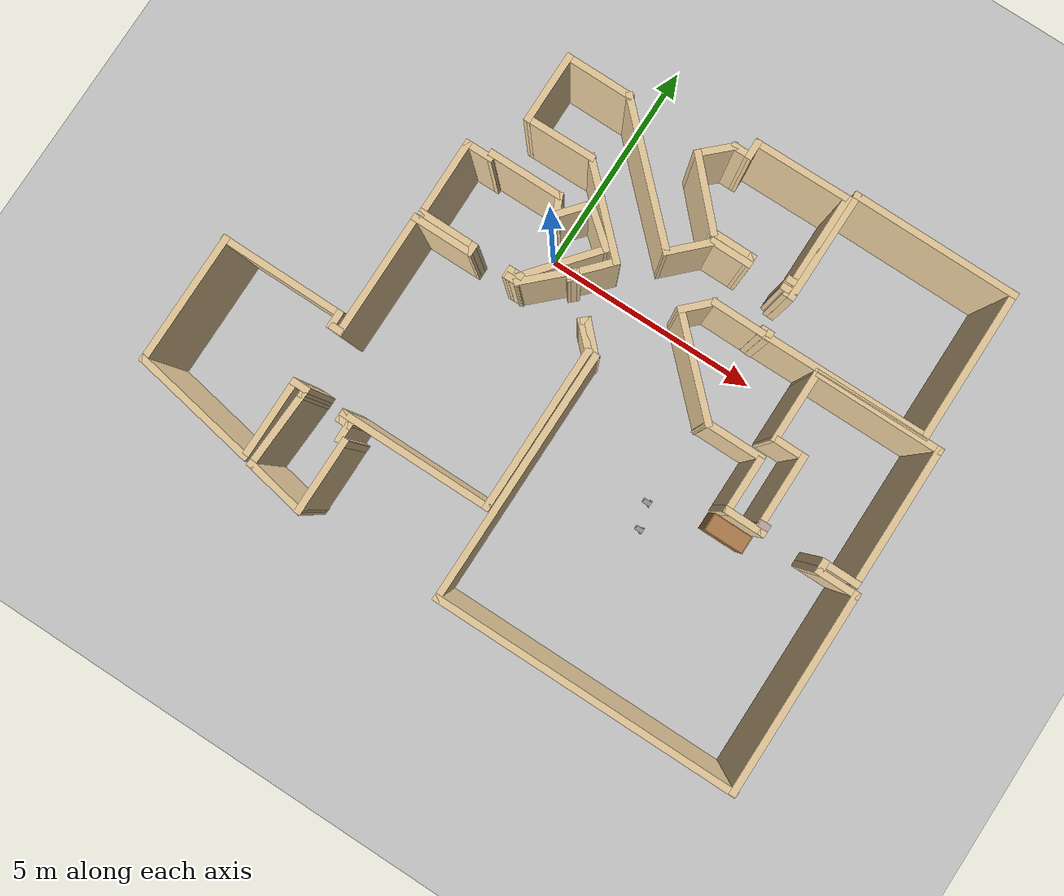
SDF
<sdf version="1.7">
 <world name="default">
  <plugin name="hello" filename="libhello.so"/>
  <light name="sun" type="directional">
   <pose>0 0 10 0 -0 0</pose>
   <diffuse>0.8 0.8 0.8 1</diffuse>
   <specular>0.2 0.2 0.2 1</specular>
   <attenuation>
    <range>1000</range>
    <constant>0.9</constant>
    <linear>0.01</linear>
    <quadratic>0.001</quadratic>
   </attenuation>
   <direction>-0.5 0.1 -0.9</direction>
   <spot><inner_angle>0</inner_angle><outer_angle>0</outer_angle><falloff>0</falloff></spot>
  </light>
  <model name="ground_plane">
   <static>1</static>
   <link name="link">
    <collision name="collision">
     <geometry><plane><normal>0 0 1</normal><size>100 100</size></plane></geometry>
     <surface>
      <contact><collide_bitmask>65535</collide_bitmask></contact>
      <friction><ode><mu>100</mu><mu2>50</mu2></ode></friction>
     </surface>
    </collision>
    <visual name="visual">
     <cast_shadows>0</cast_shadows>
     <geometry><plane><normal>0 0 1</normal><size>100 100</size></plane></geometry>
     <material>
      <script><uri>file://media/materials/scripts/gazebo.material</uri><name>Gazebo/Grey</name></script>
     </material>
    </visual>
   </link>
  </model>
  <gravity>0 0 -9.8</gravity>
  <magnetic_field>6e-06 2.3e-05 -4.2e-05</magnetic_field>
  <atmosphere type="adiabatic"/>
  <physics type="ode">
   <max_step_size>0.001</max_step_size>
   <real_time_factor>1</real_time_factor>
   <real_time_update_rate>1000</real_time_update_rate>
  </physics>
  <scene><ambient>0.4 0.4 0.4 1</ambient><background>0.7 0.7 0.7 1</background><shadows>1</shadows></scene>
  <spherical_coordinates>
   <surface_model>EARTH_WGS84</surface_model>
   <latitude_deg>0</latitude_deg>
   <longitude_deg>0</longitude_deg>
   <elevation>0</elevation>
   <heading_deg>0</heading_deg>
  </spherical_coordinates>
  <model name="apartment">
   <pose>1.66788 -1.59386 0 0 -0 0</pose>
   <link name="Wall_100">
    <collision name="Wall_100_Collision">
     <geometry><box><size>2.95149 0.15 2.5</size></box></geometry>
     <pose>0 0 1.25 0 -0 0</pose>
    </collision>
    <visual name="Wall_100_Visual">
     <pose>0 0 1.25 0 -0 0</pose>
     <geometry><box><size>2.95149 0.15 2.5</size></box></geometry>
     <material>
      <script><uri>file://media/materials/scripts/gazebo.material</uri><name>Gazebo/Grey</name></script>
      <ambient>0.921569 0.807843 0.615686 1</ambient>
     </material>
     <meta><layer>0</layer></meta>
    </visual>
    <pose>5.57024 2.17108 0 0 -0 0</pose>
   </link>
   <link name="Wall_102">
    <collision name="Wall_102_Collision">
     <geometry><box><size>3.23176 0.15 2.5</size></box></geometry>
     <pose>0 0 1.25 0 -0 0</pose>
    </collision>
    <visual name="Wall_102_Visual">
     <pose>0 0 1.25 0 -0 0</pose>
     <geometry><box><size>3.23176 0.15 2.5</size></box></geometry>
     <material>
      <script><uri>file://media/materials/scripts/gazebo.material</uri><name>Gazebo/Grey</name></script>
      <ambient>0.921569 0.807843 0.615686 1</ambient>
     </material>
     <meta><layer>0</layer></meta>
    </visual>
    <pose>6.97321 0.632438 0 0 -0 1.5708</pose>
   </link>
   <link name="Wall_104">
    <collision name="Wall_104_Collision">
     <geometry><box><size>0.864692 0.15 2.5</size></box></geometry>
     <pose>0 0 1.25 0 -0 0</pose>
    </collision>
    <visual name="Wall_104_Visual">
     <pose>0 0 1.25 0 -0 0</pose>
     <geometry><box><size>0.864692 0.15 2.5</size></box></geometry>
     <material>
      <script><uri>file://media/materials/scripts/gazebo.material</uri><name>Gazebo/Grey</name></script>
      <ambient>0.921569 0.807843 0.615686 1</ambient>
     </material>
     <meta><layer>0</layer></meta>
    </visual>
    <pose>6.61587 -0.897002 0 0 -0 0</pose>
   </link>
   <link name="Wall_106">
    <collision name="Wall_106_Collision">
     <geometry><box><size>0.346141 0.15 2.5</size></box></geometry>
     <pose>0 0 1.25 0 -0 0</pose>
    </collision>
    <visual name="Wall_106_Visual">
     <pose>0 0 1.25 0 -0 0</pose>
     <geometry><box><size>0.346141 0.15 2.5</size></box></geometry>
     <material>
      <script><uri>file://media/materials/scripts/gazebo.material</uri><name>Gazebo/Grey</name></script>
      <ambient>0.921569 0.807843 0.615686 1</ambient>
     </material>
     <meta><layer>0</layer></meta>
    </visual>
    <pose>6.24608 -0.987123 0 0 -0 -1.5708</pose>
   </link>
   <link name="Wall_107">
    <collision name="Wall_107_Collision">
     <geometry><box><size>0.990144 0.15 2.5</size></box></geometry>
     <pose>0 0 1.25 0 -0 0</pose>
    </collision>
    <visual name="Wall_107_Visual">
     <pose>0 0 1.25 0 -0 0</pose>
     <geometry><box><size>0.990144 0.15 2.5</size></box></geometry>
     <material>
      <script><uri>file://media/materials/scripts/gazebo.material</uri><name>Gazebo/Grey</name></script>
      <ambient>0.921569 0.807843 0.615686 1</ambient>
     </material>
     <meta><layer>0</layer></meta>
    </visual>
    <pose>6.66615 -1.08519 0 0 -0 0</pose>
   </link>
   <link name="Wall_109">
    <collision name="Wall_109_Collision">
     <geometry><box><size>4.58478 0.15 2.5</size></box></geometry>
     <pose>0 0 1.25 0 -0 0</pose>
    </collision>
    <visual name="Wall_109_Visual">
     <pose>0 0 1.25 0 -0 0</pose>
     <geometry><box><size>4.58478 0.15 2.5</size></box></geometry>
     <material>
      <script><uri>file://media/materials/scripts/gazebo.material</uri><name>Gazebo/Grey</name></script>
      <ambient>0.921569 0.807843 0.615686 1</ambient>
     </material>
     <meta><layer>0</layer></meta>
    </visual>
    <pose>7.08665 -3.29873 0 0 -0 -1.5708</pose>
   </link>
   <link name="Wall_11">
    <collision name="Wall_11_Collision">
     <geometry><box><size>0.284286 0.15 2.5</size></box></geometry>
     <pose>0 0 1.25 0 -0 0</pose>
    </collision>
    <visual name="Wall_11_Visual">
     <pose>0 0 1.25 0 -0 0</pose>
     <geometry><box><size>0.284286 0.15 2.5</size></box></geometry>
     <material>
      <script><uri>file://media/materials/scripts/gazebo.material</uri><name>Gazebo/Grey</name></script>
      <ambient>0.921569 0.807843 0.615686 1</ambient>
     </material>
     <meta><layer>0</layer></meta>
    </visual>
    <pose>-3.18456 -3.61653 0 0 -0 -1.58337</pose>
   </link>
   <link name="Wall_12">
    <collision name="Wall_12_Collision">
     <geometry><box><size>0.354689 0.15 2.5</size></box></geometry>
     <pose>0 0 1.25 0 -0 0</pose>
    </collision>
    <visual name="Wall_12_Visual">
     <pose>0 0 1.25 0 -0 0</pose>
     <geometry><box><size>0.354689 0.15 2.5</size></box></geometry>
     <material>
      <script><uri>file://media/materials/scripts/gazebo.material</uri><name>Gazebo/Grey</name></script>
      <ambient>0.921569 0.807843 0.615686 1</ambient>
     </material>
     <meta><layer>0</layer></meta>
    </visual>
    <pose>-3.08306 -3.68462 0 0 -0 -0.013888</pose>
   </link>
   <link name="Wall_13">
    <collision name="Wall_13_Collision">
     <geometry><box><size>0.485442 0.15 2.5</size></box></geometry>
     <pose>0 0 1.25 0 -0 0</pose>
    </collision>
    <visual name="Wall_13_Visual">
     <pose>0 0 1.25 0 -0 0</pose>
     <geometry><box><size>0.485442 0.15 2.5</size></box></geometry>
     <material>
      <script><uri>file://media/materials/scripts/gazebo.material</uri><name>Gazebo/Grey</name></script>
      <ambient>0.921569 0.807843 0.615686 1</ambient>
     </material>
     <meta><layer>0</layer></meta>
    </visual>
    <pose>-2.97931 -3.85376 0 0 -0 -1.56232</pose>
   </link>
   <link name="Wall_14">
    <collision name="Wall_14_Collision">
     <geometry><box><size>0.260899 0.15 2.5</size></box></geometry>
     <pose>0 0 1.25 0 -0 0</pose>
    </collision>
    <visual name="Wall_14_Visual">
     <pose>0 0 1.25 0 -0 0</pose>
     <geometry><box><size>0.260899 0.15 2.5</size></box></geometry>
     <material>
      <script><uri>file://media/materials/scripts/gazebo.material</uri><name>Gazebo/Grey</name></script>
      <ambient>0.921569 0.807843 0.615686 1</ambient>
     </material>
     <meta><layer>0</layer></meta>
    </visual>
    <pose>-2.92246 -4.02147 0 0 -0 0</pose>
   </link>
   <link name="Wall_17">
    <collision name="Wall_17_Collision">
     <geometry><box><size>1.73664 0.15 2.5</size></box></geometry>
     <pose>0 0 1.25 0 -0 0</pose>
    </collision>
    <visual name="Wall_17_Visual">
     <pose>0 0 1.25 0 -0 0</pose>
     <geometry><box><size>1.73664 0.15 2.5</size></box></geometry>
     <material>
      <script><uri>file://media/materials/scripts/gazebo.material</uri><name>Gazebo/Grey</name></script>
      <ambient>0.921569 0.807843 0.615686 1</ambient>
     </material>
     <meta><layer>0</layer></meta>
    </visual>
    <pose>-2.86957 -4.8027 0 0 -0 -1.56807</pose>
   </link>
   <link name="Wall_18">
    <collision name="Wall_18_Collision">
     <geometry><box><size>1.45239 0.15 2.5</size></box></geometry>
     <pose>0 0 1.25 0 -0 0</pose>
    </collision>
    <visual name="Wall_18_Visual">
     <pose>0 0 1.25 0 -0 0</pose>
     <geometry><box><size>1.45239 0.15 2.5</size></box></geometry>
     <material>
      <script><uri>file://media/materials/scripts/gazebo.material</uri><name>Gazebo/Grey</name></script>
      <ambient>0.921569 0.807843 0.615686 1</ambient>
     </material>
     <meta><layer>0</layer></meta>
    </visual>
    <pose>-3.50725 -5.47497 0 0 -0 2.95461</pose>
   </link>
   <link name="Wall_19">
    <collision name="Wall_19_Collision">
     <geometry><box><size>1.8204 0.15 2.5</size></box></geometry>
     <pose>0 0 1.25 0 -0 0</pose>
    </collision>
    <visual name="Wall_19_Visual">
     <pose>0 0 1.25 0 -0 0</pose>
     <geometry><box><size>1.8204 0.15 2.5</size></box></geometry>
     <material>
      <script><uri>file://media/materials/scripts/gazebo.material</uri><name>Gazebo/Grey</name></script>
      <ambient>0.921569 0.807843 0.615686 1</ambient>
     </material>
     <meta><layer>0</layer></meta>
    </visual>
    <pose>-4.11035 -4.51952 0 0 -0 1.52678</pose>
   </link>
   <link name="Wall_2">
    <collision name="Wall_2_Collision">
     <geometry><box><size>6.92359 0.15 2.5</size></box></geometry>
     <pose>0 0 1.25 0 -0 0</pose>
    </collision>
    <visual name="Wall_2_Visual">
     <pose>0 0 1.25 0 -0 0</pose>
     <geometry><box><size>6.92359 0.15 2.5</size></box></geometry>
     <material>
      <script><uri>file://media/materials/scripts/gazebo.material</uri><name>Gazebo/Grey</name></script>
      <ambient>0.921569 0.807843 0.615686 1</ambient>
     </material>
     <meta><layer>0</layer></meta>
    </visual>
    <pose>3.71053 -5.53361 0 0 -0 -3.1399</pose>
   </link>
   <link name="Wall_20">
    <collision name="Wall_20_Collision">
     <geometry><box><size>0.266728 0.15 2.5</size></box></geometry>
     <pose>0 0 1.25 0 -0 0</pose>
    </collision>
    <visual name="Wall_20_Visual">
     <pose>0 0 1.25 0 -0 0</pose>
     <geometry><box><size>0.266728 0.15 2.5</size></box></geometry>
     <material>
      <script><uri>file://media/materials/scripts/gazebo.material</uri><name>Gazebo/Grey</name></script>
      <ambient>0.921569 0.807843 0.615686 1</ambient>
     </material>
     <meta><layer>0</layer></meta>
    </visual>
    <pose>-4.0736 -3.62677 0 0 -0 1.5708</pose>
   </link>
   <link name="Wall_21">
    <collision name="Wall_21_Collision">
     <geometry><box><size>0.418183 0.15 2.5</size></box></geometry>
     <pose>0 0 1.25 0 -0 0</pose>
    </collision>
    <visual name="Wall_21_Visual">
     <pose>0 0 1.25 0 -0 0</pose>
     <geometry><box><size>0.418183 0.15 2.5</size></box></geometry>
     <material>
      <script><uri>file://media/materials/scripts/gazebo.material</uri><name>Gazebo/Grey</name></script>
      <ambient>0.921569 0.807843 0.615686 1</ambient>
     </material>
     <meta><layer>0</layer></meta>
    </visual>
    <pose>-4.20763 -3.5684 0 0 -0 3.14159</pose>
   </link>
   <link name="Wall_22">
    <collision name="Wall_22_Collision">
     <geometry><box><size>1.87501 0.15 2.5</size></box></geometry>
     <pose>0 0 1.25 0 -0 0</pose>
    </collision>
    <visual name="Wall_22_Visual">
     <pose>0 0 1.25 0 -0 0</pose>
     <geometry><box><size>1.87501 0.15 2.5</size></box></geometry>
     <material>
      <script><uri>file://media/materials/scripts/gazebo.material</uri><name>Gazebo/Grey</name></script>
      <ambient>0.921569 0.807843 0.615686 1</ambient>
     </material>
     <meta><layer>0</layer></meta>
    </visual>
    <pose>-4.33949 -4.4309 0 0 -0 -1.56829</pose>
   </link>
   <link name="Wall_24">
    <collision name="Wall_24_Collision">
     <geometry><box><size>2.92937 0.15 2.5</size></box></geometry>
     <pose>0 0 1.25 0 -0 0</pose>
    </collision>
    <visual name="Wall_24_Visual">
     <pose>0 0 1.25 0 -0 0</pose>
     <geometry><box><size>2.92937 0.15 2.5</size></box></geometry>
     <material>
      <script><uri>file://media/materials/scripts/gazebo.material</uri><name>Gazebo/Grey</name></script>
      <ambient>0.921569 0.807843 0.615686 1</ambient>
     </material>
     <meta><layer>0</layer></meta>
    </visual>
    <pose>-5.71608 -5.04961 0 0 -0 2.96322</pose>
   </link>
   <link name="Wall_25">
    <collision name="Wall_25_Collision">
     <geometry><box><size>3.00362 0.15 2.5</size></box></geometry>
     <pose>0 0 1.25 0 -0 0</pose>
    </collision>
    <visual name="Wall_25_Visual">
     <pose>0 0 1.25 0 -0 0</pose>
     <geometry><box><size>3.00362 0.15 2.5</size></box></geometry>
     <material>
      <script><uri>file://media/materials/scripts/gazebo.material</uri><name>Gazebo/Grey</name></script>
      <ambient>0.921569 0.807843 0.615686 1</ambient>
     </material>
     <meta><layer>0</layer></meta>
    </visual>
    <pose>-7.08371 -3.37623 0 0 -0 1.5708</pose>
   </link>
   <link name="Wall_27">
    <collision name="Wall_27_Collision">
     <geometry><box><size>2.88666 0.15 2.5</size></box></geometry>
     <pose>0 0 1.25 0 -0 0</pose>
    </collision>
    <visual name="Wall_27_Visual">
     <pose>0 0 1.25 0 -0 0</pose>
     <geometry><box><size>2.88666 0.15 2.5</size></box></geometry>
     <material>
      <script><uri>file://media/materials/scripts/gazebo.material</uri><name>Gazebo/Grey</name></script>
      <ambient>0.921569 0.807843 0.615686 1</ambient>
     </material>
     <meta><layer>0</layer></meta>
    </visual>
    <pose>-5.72877 -1.95964 0 0 -0 -0.004739</pose>
   </link>
   <link name="Wall_28">
    <collision name="Wall_28_Collision">
     <geometry><box><size>0.431046 0.15 2.5</size></box></geometry>
     <pose>0 0 1.25 0 -0 0</pose>
    </collision>
    <visual name="Wall_28_Visual">
     <pose>0 0 1.25 0 -0 0</pose>
     <geometry><box><size>0.431046 0.15 2.5</size></box></geometry>
     <material>
      <script><uri>file://media/materials/scripts/gazebo.material</uri><name>Gazebo/Grey</name></script>
      <ambient>0.921569 0.807843 0.615686 1</ambient>
     </material>
     <meta><layer>0</layer></meta>
    </visual>
    <pose>-4.36045 -2.10663 0 0 -0 -1.5708</pose>
   </link>
   <link name="Wall_29">
    <collision name="Wall_29_Collision">
     <geometry><box><size>0.335901 0.15 2.5</size></box></geometry>
     <pose>0 0 1.25 0 -0 0</pose>
    </collision>
    <visual name="Wall_29_Visual">
     <pose>0 0 1.25 0 -0 0</pose>
     <geometry><box><size>0.335901 0.15 2.5</size></box></geometry>
     <material>
      <script><uri>file://media/materials/scripts/gazebo.material</uri><name>Gazebo/Grey</name></script>
      <ambient>0.921569 0.807843 0.615686 1</ambient>
     </material>
     <meta><layer>0</layer></meta>
    </visual>
    <pose>-4.2675 -2.24714 0 0 -0 0</pose>
   </link>
   <link name="Wall_3">
    <collision name="Wall_3_Collision">
     <geometry><box><size>5.75051 0.15 2.5</size></box></geometry>
     <pose>0 0 1.25 0 -0 0</pose>
    </collision>
    <visual name="Wall_3_Visual">
     <pose>0 0 1.25 0 -0 0</pose>
     <geometry><box><size>5.75051 0.15 2.5</size></box></geometry>
     <material>
      <script><uri>file://media/materials/scripts/gazebo.material</uri><name>Gazebo/Grey</name></script>
      <ambient>0.921569 0.807843 0.615686 1</ambient>
     </material>
     <meta><layer>0</layer></meta>
    </visual>
    <pose>0.329528 -2.73911 0 0 -0 1.56874</pose>
   </link>
   <link name="Wall_31">
    <collision name="Wall_31_Collision">
     <geometry><box><size>2.85962 0.15 2.5</size></box></geometry>
     <pose>0 0 1.25 0 -0 0</pose>
    </collision>
    <visual name="Wall_31_Visual">
     <pose>0 0 1.25 0 -0 0</pose>
     <geometry><box><size>2.85962 0.15 2.5</size></box></geometry>
     <material>
      <script><uri>file://media/materials/scripts/gazebo.material</uri><name>Gazebo/Grey</name></script>
      <ambient>0.921569 0.807843 0.615686 1</ambient>
     </material>
     <meta><layer>0</layer></meta>
    </visual>
    <pose>-4.15578 -0.899039 0 0 -0 1.57263</pose>
   </link>
   <link name="Wall_32">
    <collision name="Wall_32_Collision">
     <geometry><box><size>1.42278 0.15 2.5</size></box></geometry>
     <pose>0 0 1.25 0 -0 0</pose>
    </collision>
    <visual name="Wall_32_Visual">
     <pose>0 0 1.25 0 -0 0</pose>
     <geometry><box><size>1.42278 0.15 2.5</size></box></geometry>
     <material>
      <script><uri>file://media/materials/scripts/gazebo.material</uri><name>Gazebo/Grey</name></script>
      <ambient>0.921569 0.807843 0.615686 1</ambient>
     </material>
     <meta><layer>0</layer></meta>
    </visual>
    <pose>-3.52188 0.458253 0 0 -0 0.003906</pose>
   </link>
   <link name="Wall_33">
    <collision name="Wall_33_Collision">
     <geometry><box><size>0.294181 0.15 2.5</size></box></geometry>
     <pose>0 0 1.25 0 -0 0</pose>
    </collision>
    <visual name="Wall_33_Visual">
     <pose>0 0 1.25 0 -0 0</pose>
     <geometry><box><size>0.294181 0.15 2.5</size></box></geometry>
     <material>
      <script><uri>file://media/materials/scripts/gazebo.material</uri><name>Gazebo/Grey</name></script>
      <ambient>0.921569 0.807843 0.615686 1</ambient>
     </material>
     <meta><layer>0</layer></meta>
    </visual>
    <pose>-2.88549 0.53283 0 0 -0 1.5708</pose>
   </link>
   <link name="Wall_34">
    <collision name="Wall_34_Collision">
     <geometry><box><size>1.37315 0.15 2.5</size></box></geometry>
     <pose>0 0 1.25 0 -0 0</pose>
    </collision>
    <visual name="Wall_34_Visual">
     <pose>0 0 1.25 0 -0 0</pose>
     <geometry><box><size>1.37315 0.15 2.5</size></box></geometry>
     <material>
      <script><uri>file://media/materials/scripts/gazebo.material</uri><name>Gazebo/Grey</name></script>
      <ambient>0.921569 0.807843 0.615686 1</ambient>
     </material>
     <meta><layer>0</layer></meta>
    </visual>
    <pose>-3.49702 0.607406 0 0 -0 3.13753</pose>
   </link>
   <link name="Wall_36">
    <collision name="Wall_36_Collision">
     <geometry><box><size>1.80158 0.15 2.5</size></box></geometry>
     <pose>0 0 1.25 0 -0 0</pose>
    </collision>
    <visual name="Wall_36_Visual">
     <pose>0 0 1.25 0 -0 0</pose>
     <geometry><box><size>1.80158 0.15 2.5</size></box></geometry>
     <material>
      <script><uri>file://media/materials/scripts/gazebo.material</uri><name>Gazebo/Grey</name></script>
      <ambient>0.921569 0.807843 0.615686 1</ambient>
     </material>
     <meta><layer>0</layer></meta>
    </visual>
    <pose>-4.11695 1.45041 0 0 -0 1.58127</pose>
   </link>
   <link name="Wall_37">
    <collision name="Wall_37_Collision">
     <geometry><box><size>0.681781 0.15 2.5</size></box></geometry>
     <pose>0 0 1.25 0 -0 0</pose>
    </collision>
    <visual name="Wall_37_Visual">
     <pose>0 0 1.25 0 -0 0</pose>
     <geometry><box><size>0.681781 0.15 2.5</size></box></geometry>
     <material>
      <script><uri>file://media/materials/scripts/gazebo.material</uri><name>Gazebo/Grey</name></script>
      <ambient>0.921569 0.807843 0.615686 1</ambient>
     </material>
     <meta><layer>0</layer></meta>
    </visual>
    <pose>-3.85972 2.27831 0 0 -0 0.00813</pose>
   </link>
   <link name="Wall_38">
    <collision name="Wall_38_Collision">
     <geometry><box><size>0.245504 0.15 2.5</size></box></geometry>
     <pose>0 0 1.25 0 -0 0</pose>
    </collision>
    <visual name="Wall_38_Visual">
     <pose>0 0 1.25 0 -0 0</pose>
     <geometry><box><size>0.245504 0.15 2.5</size></box></geometry>
     <material>
      <script><uri>file://media/materials/scripts/gazebo.material</uri><name>Gazebo/Grey</name></script>
      <ambient>0.921569 0.807843 0.615686 1</ambient>
     </material>
     <meta><layer>0</layer></meta>
    </visual>
    <pose>-3.59383 2.32803 0 0 -0 1.5708</pose>
   </link>
   <link name="Wall_39">
    <collision name="Wall_39_Collision">
     <geometry><box><size>1.72802 0.15 2.5</size></box></geometry>
     <pose>0 0 1.25 0 -0 0</pose>
    </collision>
    <visual name="Wall_39_Visual">
     <pose>0 0 1.25 0 -0 0</pose>
     <geometry><box><size>1.72802 0.15 2.5</size></box></geometry>
     <material>
      <script><uri>file://media/materials/scripts/gazebo.material</uri><name>Gazebo/Grey</name></script>
      <ambient>0.921569 0.807843 0.615686 1</ambient>
     </material>
     <meta><layer>0</layer></meta>
    </visual>
    <pose>-2.80484 2.37991 0 0 -0 0.005479</pose>
   </link>
   <link name="Wall_4">
    <collision name="Wall_4_Collision">
     <geometry><box><size>0.890032 0.15 2.5</size></box></geometry>
     <pose>0 0 1.25 0 -0 0</pose>
    </collision>
    <visual name="Wall_4_Visual">
     <pose>0 0 1.25 0 -0 0</pose>
     <geometry><box><size>0.890032 0.15 2.5</size></box></geometry>
     <material>
      <script><uri>file://media/materials/scripts/gazebo.material</uri><name>Gazebo/Grey</name></script>
      <ambient>0.921569 0.807843 0.615686 1</ambient>
     </material>
     <meta><layer>0</layer></meta>
    </visual>
    <pose>0.076528 0.32564 0 0 -0 2.34521</pose>
   </link>
   <link name="Wall_40">
    <collision name="Wall_40_Collision">
     <geometry><box><size>0.537169 0.15 2.5</size></box></geometry>
     <pose>0 0 1.25 0 -0 0</pose>
    </collision>
    <visual name="Wall_40_Visual">
     <pose>0 0 1.25 0 -0 0</pose>
     <geometry><box><size>0.537169 0.15 2.5</size></box></geometry>
     <material>
      <script><uri>file://media/materials/scripts/gazebo.material</uri><name>Gazebo/Grey</name></script>
      <ambient>0.921569 0.807843 0.615686 1</ambient>
     </material>
     <meta><layer>0</layer></meta>
    </visual>
    <pose>-1.93802 2.20698 0 0 -0 -1.15711</pose>
   </link>
   <link name="Wall_41">
    <collision name="Wall_41_Collision">
     <geometry><box><size>0.882932 0.15 2.5</size></box></geometry>
     <pose>0 0 1.25 0 -0 0</pose>
    </collision>
    <visual name="Wall_41_Visual">
     <pose>0 0 1.25 0 -0 0</pose>
     <geometry><box><size>0.882932 0.15 2.5</size></box></geometry>
     <material>
      <script><uri>file://media/materials/scripts/gazebo.material</uri><name>Gazebo/Grey</name></script>
      <ambient>0.921569 0.807843 0.615686 1</ambient>
     </material>
     <meta><layer>0</layer></meta>
    </visual>
    <pose>-1.62458 2.31074 0 0 -0 0.873039</pose>
   </link>
   <link name="Wall_42">
    <collision name="Wall_42_Collision">
     <geometry><box><size>1.10544 0.15 2.5</size></box></geometry>
     <pose>0 0 1.25 0 -0 0</pose>
    </collision>
    <visual name="Wall_42_Visual">
     <pose>0 0 1.25 0 -0 0</pose>
     <geometry><box><size>1.10544 0.15 2.5</size></box></geometry>
     <material>
      <script><uri>file://media/materials/scripts/gazebo.material</uri><name>Gazebo/Grey</name></script>
      <ambient>0.921569 0.807843 0.615686 1</ambient>
     </material>
     <meta><layer>0</layer></meta>
    </visual>
    <pose>-1.01932 2.28912 0 0 -0 -0.686048</pose>
   </link>
   <link name="Wall_43">
    <collision name="Wall_43_Collision">
     <geometry><box><size>1.94016 0.15 2.5</size></box></geometry>
     <pose>0 0 1.25 0 -0 0</pose>
    </collision>
    <visual name="Wall_43_Visual">
     <pose>0 0 1.25 0 -0 0</pose>
     <geometry><box><size>1.94016 0.15 2.5</size></box></geometry>
     <material>
      <script><uri>file://media/materials/scripts/gazebo.material</uri><name>Gazebo/Grey</name></script>
      <ambient>0.921569 0.807843 0.615686 1</ambient>
     </material>
     <meta><layer>0</layer></meta>
    </visual>
    <pose>-1.22036 1.29693 0 0 -0 -2.26213</pose>
   </link>
   <link name="Wall_44">
    <collision name="Wall_44_Collision">
     <geometry><box><size>0.361885 0.15 2.5</size></box></geometry>
     <pose>0 0 1.25 0 -0 0</pose>
    </collision>
    <visual name="Wall_44_Visual">
     <pose>0 0 1.25 0 -0 0</pose>
     <geometry><box><size>0.361885 0.15 2.5</size></box></geometry>
     <material>
      <script><uri>file://media/materials/scripts/gazebo.material</uri><name>Gazebo/Grey</name></script>
      <ambient>0.921569 0.807843 0.615686 1</ambient>
     </material>
     <meta><layer>0</layer></meta>
    </visual>
    <pose>-1.89695 0.605206 0 0 -0 -3.12119</pose>
   </link>
   <link name="Wall_45">
    <collision name="Wall_45_Collision">
     <geometry><box><size>0.27977 0.15 2.5</size></box></geometry>
     <pose>0 0 1.25 0 -0 0</pose>
    </collision>
    <visual name="Wall_45_Visual">
     <pose>0 0 1.25 0 -0 0</pose>
     <geometry><box><size>0.27977 0.15 2.5</size></box></geometry>
     <material>
      <script><uri>file://media/materials/scripts/gazebo.material</uri><name>Gazebo/Grey</name></script>
      <ambient>0.921569 0.807843 0.615686 1</ambient>
     </material>
     <meta><layer>0</layer></meta>
    </visual>
    <pose>-2.00287 0.538195 0 0 -0 -1.5708</pose>
   </link>
   <link name="Wall_46">
    <collision name="Wall_46_Collision">
     <geometry><box><size>0.383497 0.15 2.5</size></box></geometry>
     <pose>0 0 1.25 0 -0 0</pose>
    </collision>
    <visual name="Wall_46_Visual">
     <pose>0 0 1.25 0 -0 0</pose>
     <geometry><box><size>0.383497 0.15 2.5</size></box></geometry>
     <material>
      <script><uri>file://media/materials/scripts/gazebo.material</uri><name>Gazebo/Grey</name></script>
      <ambient>0.921569 0.807843 0.615686 1</ambient>
     </material>
     <meta><layer>0</layer></meta>
    </visual>
    <pose>-1.88614 0.475507 0 0 -0 0.018516</pose>
   </link>
   <link name="Wall_47">
    <collision name="Wall_47_Collision">
     <geometry><box><size>1.19266 0.15 2.5</size></box></geometry>
     <pose>0 0 1.25 0 -0 0</pose>
    </collision>
    <visual name="Wall_47_Visual">
     <pose>0 0 1.25 0 -0 0</pose>
     <geometry><box><size>1.19266 0.15 2.5</size></box></geometry>
     <material>
      <script><uri>file://media/materials/scripts/gazebo.material</uri><name>Gazebo/Grey</name></script>
      <ambient>0.921569 0.807843 0.615686 1</ambient>
     </material>
     <meta><layer>0</layer></meta>
    </visual>
    <pose>-1.39329 0.838663 0 0 -0 0.764873</pose>
   </link>
   <link name="Wall_48">
    <collision name="Wall_48_Collision">
     <geometry><box><size>0.272281 0.15 2.5</size></box></geometry>
     <pose>0 0 1.25 0 -0 0</pose>
    </collision>
    <visual name="Wall_48_Visual">
     <pose>0 0 1.25 0 -0 0</pose>
     <geometry><box><size>0.272281 0.15 2.5</size></box></geometry>
     <material>
      <script><uri>file://media/materials/scripts/gazebo.material</uri><name>Gazebo/Grey</name></script>
      <ambient>0.921569 0.807843 0.615686 1</ambient>
     </material>
     <meta><layer>0</layer></meta>
    </visual>
    <pose>-0.973929 1.15642 0 0 -0 -0.785398</pose>
   </link>
   <link name="Wall_49">
    <collision name="Wall_49_Collision">
     <geometry><box><size>0.272433 0.15 2.5</size></box></geometry>
     <pose>0 0 1.25 0 -0 0</pose>
    </collision>
    <visual name="Wall_49_Visual">
     <pose>0 0 1.25 0 -0 0</pose>
     <geometry><box><size>0.272433 0.15 2.5</size></box></geometry>
     <material>
      <script><uri>file://media/materials/scripts/gazebo.material</uri><name>Gazebo/Grey</name></script>
      <ambient>0.921569 0.807843 0.615686 1</ambient>
     </material>
     <meta><layer>0</layer></meta>
    </visual>
    <pose>-0.885302 1.15426 0 0 -0 0.73544</pose>
   </link>
   <link name="Wall_5">
    <collision name="Wall_5_Collision">
     <geometry><box><size>0.272247 0.15 2.5</size></box></geometry>
     <pose>0 0 1.25 0 -0 0</pose>
    </collision>
    <visual name="Wall_5_Visual">
     <pose>0 0 1.25 0 -0 0</pose>
     <geometry><box><size>0.272247 0.15 2.5</size></box></geometry>
     <material>
      <script><uri>file://media/materials/scripts/gazebo.material</uri><name>Gazebo/Grey</name></script>
      <ambient>0.921569 0.807843 0.615686 1</ambient>
     </material>
     <meta><layer>0</layer></meta>
    </visual>
    <pose>-0.228222 0.54989 0 0 -0 -2.42276</pose>
   </link>
   <link name="Wall_50">
    <collision name="Wall_50_Collision">
     <geometry><box><size>0.248015 0.15 2.5</size></box></geometry>
     <pose>0 0 1.25 0 -0 0</pose>
    </collision>
    <visual name="Wall_50_Visual">
     <pose>0 0 1.25 0 -0 0</pose>
     <geometry><box><size>0.248015 0.15 2.5</size></box></geometry>
     <material>
      <script><uri>file://media/materials/scripts/gazebo.material</uri><name>Gazebo/Grey</name></script>
      <ambient>0.921569 0.807843 0.615686 1</ambient>
     </material>
     <meta><layer>0</layer></meta>
    </visual>
    <pose>-0.872332 1.23208 0 0 -0 2.29378</pose>
   </link>
   <link name="Wall_51">
    <collision name="Wall_51_Collision">
     <geometry><box><size>0.963994 0.15 2.5</size></box></geometry>
     <pose>0 0 1.25 0 -0 0</pose>
    </collision>
    <visual name="Wall_51_Visual">
     <pose>0 0 1.25 0 -0 0</pose>
     <geometry><box><size>0.963994 0.15 2.5</size></box></geometry>
     <material>
      <script><uri>file://media/materials/scripts/gazebo.material</uri><name>Gazebo/Grey</name></script>
      <ambient>0.921569 0.807843 0.615686 1</ambient>
     </material>
     <meta><layer>0</layer></meta>
    </visual>
    <pose>-0.630228 1.5693 0 0 -0 0.83048</pose>
   </link>
   <link name="Wall_53">
    <collision name="Wall_53_Collision">
     <geometry><box><size>2.31242 0.15 2.5</size></box></geometry>
     <pose>0 0 1.25 0 -0 0</pose>
    </collision>
    <visual name="Wall_53_Visual">
     <pose>0 0 1.25 0 -0 0</pose>
     <geometry><box><size>2.31242 0.15 2.5</size></box></geometry>
     <material>
      <script><uri>file://media/materials/scripts/gazebo.material</uri><name>Gazebo/Grey</name></script>
      <ambient>0.921569 0.807843 0.615686 1</ambient>
     </material>
     <meta><layer>0</layer></meta>
    </visual>
    <pose>-1.12607 2.63616 0 0 -0 2.37408</pose>
   </link>
   <link name="Wall_54">
    <collision name="Wall_54_Collision">
     <geometry><box><size>1.63669 0.15 2.5</size></box></geometry>
     <pose>0 0 1.25 0 -0 0</pose>
    </collision>
    <visual name="Wall_54_Visual">
     <pose>0 0 1.25 0 -0 0</pose>
     <geometry><box><size>1.63669 0.15 2.5</size></box></geometry>
     <material>
      <script><uri>file://media/materials/scripts/gazebo.material</uri><name>Gazebo/Grey</name></script>
      <ambient>0.921569 0.807843 0.615686 1</ambient>
     </material>
     <meta><layer>0</layer></meta>
    </visual>
    <pose>-2.64743 3.37695 0 0 -0 -3.12822</pose>
   </link>
   <link name="Wall_55">
    <collision name="Wall_55_Collision">
     <geometry><box><size>1.64651 0.15 2.5</size></box></geometry>
     <pose>0 0 1.25 0 -0 0</pose>
    </collision>
    <visual name="Wall_55_Visual">
     <pose>0 0 1.25 0 -0 0</pose>
     <geometry><box><size>1.64651 0.15 2.5</size></box></geometry>
     <material>
      <script><uri>file://media/materials/scripts/gazebo.material</uri><name>Gazebo/Grey</name></script>
      <ambient>0.921569 0.807843 0.615686 1</ambient>
     </material>
     <meta><layer>0</layer></meta>
    </visual>
    <pose>-3.39319 4.11526 0 0 -0 1.57412</pose>
   </link>
   <link name="Wall_56">
    <collision name="Wall_56_Collision">
     <geometry><box><size>1.59679 0.15 2.5</size></box></geometry>
     <pose>0 0 1.25 0 -0 0</pose>
    </collision>
    <visual name="Wall_56_Visual">
     <pose>0 0 1.25 0 -0 0</pose>
     <geometry><box><size>1.59679 0.15 2.5</size></box></geometry>
     <material>
      <script><uri>file://media/materials/scripts/gazebo.material</uri><name>Gazebo/Grey</name></script>
      <ambient>0.921569 0.807843 0.615686 1</ambient>
     </material>
     <meta><layer>0</layer></meta>
    </visual>
    <pose>-2.67229 4.86102 0 0 -0 -0.003436</pose>
   </link>
   <link name="Wall_57">
    <collision name="Wall_57_Collision">
     <geometry><box><size>3.39866 0.15 2.5</size></box></geometry>
     <pose>0 0 1.25 0 -0 0</pose>
    </collision>
    <visual name="Wall_57_Visual">
     <pose>0 0 1.25 0 -0 0</pose>
     <geometry><box><size>3.39866 0.15 2.5</size></box></geometry>
     <material>
      <script><uri>file://media/materials/scripts/gazebo.material</uri><name>Gazebo/Grey</name></script>
      <ambient>0.921569 0.807843 0.615686 1</ambient>
     </material>
     <meta><layer>0</layer></meta>
    </visual>
    <pose>-0.785501 3.72497 0 0 -0 -0.772412</pose>
   </link>
   <link name="Wall_58">
    <collision name="Wall_58_Collision">
     <geometry><box><size>1.11679 0.15 2.5</size></box></geometry>
     <pose>0 0 1.25 0 -0 0</pose>
    </collision>
    <visual name="Wall_58_Visual">
     <pose>0 0 1.25 0 -0 0</pose>
     <geometry><box><size>1.11679 0.15 2.5</size></box></geometry>
     <material>
      <script><uri>file://media/materials/scripts/gazebo.material</uri><name>Gazebo/Grey</name></script>
      <ambient>0.921569 0.807843 0.615686 1</ambient>
     </material>
     <meta><layer>0</layer></meta>
    </visual>
    <pose>0.720944 2.93197 0 0 -0 0.781762</pose>
   </link>
   <link name="Wall_59">
    <collision name="Wall_59_Collision">
     <geometry><box><size>0.950593 0.15 2.5</size></box></geometry>
     <pose>0 0 1.25 0 -0 0</pose>
    </collision>
    <visual name="Wall_59_Visual">
     <pose>0 0 1.25 0 -0 0</pose>
     <geometry><box><size>0.950593 0.15 2.5</size></box></geometry>
     <material>
      <script><uri>file://media/materials/scripts/gazebo.material</uri><name>Gazebo/Grey</name></script>
      <ambient>0.921569 0.807843 0.615686 1</ambient>
     </material>
     <meta><layer>0</layer></meta>
    </visual>
    <pose>1.46422 3.27254 0 0 -0 0</pose>
   </link>
   <link name="Wall_6">
    <collision name="Wall_6_Collision">
     <geometry><box><size>0.759934 0.15 2.5</size></box></geometry>
     <pose>0 0 1.25 0 -0 0</pose>
    </collision>
    <visual name="Wall_6_Visual">
     <pose>0 0 1.25 0 -0 0</pose>
     <geometry><box><size>0.759934 0.15 2.5</size></box></geometry>
     <material>
      <script><uri>file://media/materials/scripts/gazebo.material</uri><name>Gazebo/Grey</name></script>
      <ambient>0.921569 0.807843 0.615686 1</ambient>
     </material>
     <meta><layer>0</layer></meta>
    </visual>
    <pose>-0.055722 0.29689 0 0 -0 -0.772066</pose>
   </link>
   <link name="Wall_60">
    <collision name="Wall_60_Collision">
     <geometry><box><size>0.299153 0.15 2.5</size></box></geometry>
     <pose>0 0 1.25 0 -0 0</pose>
    </collision>
    <visual name="Wall_60_Visual">
     <pose>0 0 1.25 0 -0 0</pose>
     <geometry><box><size>0.299153 0.15 2.5</size></box></geometry>
     <material>
      <script><uri>file://media/materials/scripts/gazebo.material</uri><name>Gazebo/Grey</name></script>
      <ambient>0.921569 0.807843 0.615686 1</ambient>
     </material>
     <meta><layer>0</layer></meta>
    </visual>
    <pose>1.86197 3.34712 0 0 -0 1.60412</pose>
   </link>
   <link name="Wall_61">
    <collision name="Wall_61_Collision">
     <geometry><box><size>1.0499 0.15 2.5</size></box></geometry>
     <pose>0 0 1.25 0 -0 0</pose>
    </collision>
    <visual name="Wall_61_Visual">
     <pose>0 0 1.25 0 -0 0</pose>
     <geometry><box><size>1.0499 0.15 2.5</size></box></geometry>
     <material>
      <script><uri>file://media/materials/scripts/gazebo.material</uri><name>Gazebo/Grey</name></script>
      <ambient>0.921569 0.807843 0.615686 1</ambient>
     </material>
     <meta><layer>0</layer></meta>
    </visual>
    <pose>1.40953 3.42418 0 0 -0 3.13607</pose>
   </link>
   <link name="Wall_62">
    <collision name="Wall_62_Collision">
     <geometry><box><size>1.78177 0.15 2.5</size></box></geometry>
     <pose>0 0 1.25 0 -0 0</pose>
    </collision>
    <visual name="Wall_62_Visual">
     <pose>0 0 1.25 0 -0 0</pose>
     <geometry><box><size>1.78177 0.15 2.5</size></box></geometry>
     <material>
      <script><uri>file://media/materials/scripts/gazebo.material</uri><name>Gazebo/Grey</name></script>
      <ambient>0.921569 0.807843 0.615686 1</ambient>
     </material>
     <meta><layer>0</layer></meta>
    </visual>
    <pose>0.39778 4.01831 0 0 -0 2.33034</pose>
   </link>
   <link name="Wall_64">
    <collision name="Wall_64_Collision">
     <geometry><box><size>0.902628 0.15 2.5</size></box></geometry>
     <pose>0 0 1.25 0 -0 0</pose>
    </collision>
    <visual name="Wall_64_Visual">
     <pose>0 0 1.25 0 -0 0</pose>
     <geometry><box><size>0.902628 0.15 2.5</size></box></geometry>
     <material>
      <script><uri>file://media/materials/scripts/gazebo.material</uri><name>Gazebo/Grey</name></script>
      <ambient>0.921569 0.807843 0.615686 1</ambient>
     </material>
     <meta><layer>0</layer></meta>
    </visual>
    <pose>0.104445 4.87345 0 0 -0 0.757368</pose>
   </link>
   <link name="Wall_65">
    <collision name="Wall_65_Collision">
     <geometry><box><size>0.498024 0.15 2.5</size></box></geometry>
     <pose>0 0 1.25 0 -0 0</pose>
    </collision>
    <visual name="Wall_65_Visual">
     <pose>0 0 1.25 0 -0 0</pose>
     <geometry><box><size>0.498024 0.15 2.5</size></box></geometry>
     <material>
      <script><uri>file://media/materials/scripts/gazebo.material</uri><name>Gazebo/Grey</name></script>
      <ambient>0.921569 0.807843 0.615686 1</ambient>
     </material>
     <meta><layer>0</layer></meta>
    </visual>
    <pose>0.551904 5.13198 0 0 -0 0</pose>
   </link>
   <link name="Wall_66">
    <collision name="Wall_66_Collision">
     <geometry><box><size>0.453319 0.15 2.5</size></box></geometry>
     <pose>0 0 1.25 0 -0 0</pose>
    </collision>
    <visual name="Wall_66_Visual">
     <pose>0 0 1.25 0 -0 0</pose>
     <geometry><box><size>0.453319 0.15 2.5</size></box></geometry>
     <material>
      <script><uri>file://media/materials/scripts/gazebo.material</uri><name>Gazebo/Grey</name></script>
      <ambient>0.921569 0.807843 0.615686 1</ambient>
     </material>
     <meta><layer>0</layer></meta>
    </visual>
    <pose>0.72343 5.28362 0 0 -0 1.58719</pose>
   </link>
   <link name="Wall_67">
    <collision name="Wall_67_Collision">
     <geometry><box><size>2.25311 0.15 2.5</size></box></geometry>
     <pose>0 0 1.25 0 -0 0</pose>
    </collision>
    <visual name="Wall_67_Visual">
     <pose>0 0 1.25 0 -0 0</pose>
     <geometry><box><size>2.25311 0.15 2.5</size></box></geometry>
     <material>
      <script><uri>file://media/materials/scripts/gazebo.material</uri><name>Gazebo/Grey</name></script>
      <ambient>0.921569 0.807843 0.615686 1</ambient>
     </material>
     <meta><layer>0</layer></meta>
    </visual>
    <pose>1.77247 5.44272 0 0 -0 0.007092</pose>
   </link>
   <link name="Wall_68">
    <collision name="Wall_68_Collision">
     <geometry><box><size>2.15362 0.15 2.5</size></box></geometry>
     <pose>0 0 1.25 0 -0 0</pose>
    </collision>
    <visual name="Wall_68_Visual">
     <pose>0 0 1.25 0 -0 0</pose>
     <geometry><box><size>2.15362 0.15 2.5</size></box></geometry>
     <material>
      <script><uri>file://media/materials/scripts/gazebo.material</uri><name>Gazebo/Grey</name></script>
      <ambient>0.921569 0.807843 0.615686 1</ambient>
     </material>
     <meta><layer>0</layer></meta>
    </visual>
    <pose>2.824 4.44836 0 0 -0 -1.5708</pose>
   </link>
   <link name="Wall_69">
    <collision name="Wall_69_Collision">
     <geometry><box><size>0.23452 0.15 2.5</size></box></geometry>
     <pose>0 0 1.25 0 -0 0</pose>
    </collision>
    <visual name="Wall_69_Visual">
     <pose>0 0 1.25 0 -0 0</pose>
     <geometry><box><size>0.23452 0.15 2.5</size></box></geometry>
     <material>
      <script><uri>file://media/materials/scripts/gazebo.material</uri><name>Gazebo/Grey</name></script>
      <ambient>0.921569 0.807843 0.615686 1</ambient>
     </material>
     <meta><layer>0</layer></meta>
    </visual>
    <pose>2.78174 3.44655 0 0 -0 3.14159</pose>
   </link>
   <link name="Wall_7">
    <collision name="Wall_7_Collision">
     <geometry><box><size>3.784 0.15 2.5</size></box></geometry>
     <pose>0 0 1.25 0 -0 0</pose>
    </collision>
    <visual name="Wall_7_Visual">
     <pose>0 0 1.25 0 -0 0</pose>
     <geometry><box><size>3.784 0.15 2.5</size></box></geometry>
     <material>
      <script><uri>file://media/materials/scripts/gazebo.material</uri><name>Gazebo/Grey</name></script>
      <ambient>0.921569 0.807843 0.615686 1</ambient>
     </material>
     <meta><layer>0</layer></meta>
    </visual>
    <pose>0.162778 -1.73286 0 0 -0 -1.5708</pose>
   </link>
   <link name="Wall_71">
    <collision name="Wall_71_Collision">
     <geometry><box><size>0.334904 0.15 2.5</size></box></geometry>
     <pose>0 0 1.25 0 -0 0</pose>
    </collision>
    <visual name="Wall_71_Visual">
     <pose>0 0 1.25 0 -0 0</pose>
     <geometry><box><size>0.334904 0.15 2.5</size></box></geometry>
     <material>
      <script><uri>file://media/materials/scripts/gazebo.material</uri><name>Gazebo/Grey</name></script>
      <ambient>0.921569 0.807843 0.615686 1</ambient>
     </material>
     <meta><layer>0</layer></meta>
    </visual>
    <pose>2.72936 3.35367 0 0 -0 -1.58814</pose>
   </link>
   <link name="Wall_72">
    <collision name="Wall_72_Collision">
     <geometry><box><size>0.251572 0.15 2.5</size></box></geometry>
     <pose>0 0 1.25 0 -0 0</pose>
    </collision>
    <visual name="Wall_72_Visual">
     <pose>0 0 1.25 0 -0 0</pose>
     <geometry><box><size>0.251572 0.15 2.5</size></box></geometry>
     <material>
      <script><uri>file://media/materials/scripts/gazebo.material</uri><name>Gazebo/Grey</name></script>
      <ambient>0.921569 0.807843 0.615686 1</ambient>
     </material>
     <meta><layer>0</layer></meta>
    </visual>
    <pose>2.77852 3.26123 0 0 -0 0</pose>
   </link>
   <link name="Wall_73">
    <collision name="Wall_73_Collision">
     <geometry><box><size>0.222676 0.15 2.5</size></box></geometry>
     <pose>0 0 1.25 0 -0 0</pose>
    </collision>
    <visual name="Wall_73_Visual">
     <pose>0 0 1.25 0 -0 0</pose>
     <geometry><box><size>0.222676 0.15 2.5</size></box></geometry>
     <material>
      <script><uri>file://media/materials/scripts/gazebo.material</uri><name>Gazebo/Grey</name></script>
      <ambient>0.921569 0.807843 0.615686 1</ambient>
     </material>
     <meta><layer>0</layer></meta>
    </visual>
    <pose>2.82928 3.2249 0 0 -0 -1.5708</pose>
   </link>
   <link name="Wall_74">
    <collision name="Wall_74_Collision">
     <geometry><box><size>0.264345 0.15 2.5</size></box></geometry>
     <pose>0 0 1.25 0 -0 0</pose>
    </collision>
    <visual name="Wall_74_Visual">
     <pose>0 0 1.25 0 -0 0</pose>
     <geometry><box><size>0.264345 0.15 2.5</size></box></geometry>
     <material>
      <script><uri>file://media/materials/scripts/gazebo.material</uri><name>Gazebo/Grey</name></script>
      <ambient>0.921569 0.807843 0.615686 1</ambient>
     </material>
     <meta><layer>0</layer></meta>
    </visual>
    <pose>2.88645 3.18857 0 0 -0 0</pose>
   </link>
   <link name="Wall_76">
    <collision name="Wall_76_Collision">
     <geometry><box><size>2.57539 0.15 2.5</size></box></geometry>
     <pose>0 0 1.25 0 -0 0</pose>
    </collision>
    <visual name="Wall_76_Visual">
     <pose>0 0 1.25 0 -0 0</pose>
     <geometry><box><size>2.57539 0.15 2.5</size></box></geometry>
     <material>
      <script><uri>file://media/materials/scripts/gazebo.material</uri><name>Gazebo/Grey</name></script>
      <ambient>0.921569 0.807843 0.615686 1</ambient>
     </material>
     <meta><layer>0</layer></meta>
    </visual>
    <pose>2.95481 4.39558 0 0 -0 1.56545</pose>
   </link>
   <link name="Wall_77">
    <collision name="Wall_77_Collision">
     <geometry><box><size>3.79022 0.15 2.5</size></box></geometry>
     <pose>0 0 1.25 0 -0 0</pose>
    </collision>
    <visual name="Wall_77_Visual">
     <pose>0 0 1.25 0 -0 0</pose>
     <geometry><box><size>3.79022 0.15 2.5</size></box></geometry>
     <material>
      <script><uri>file://media/materials/scripts/gazebo.material</uri><name>Gazebo/Grey</name></script>
      <ambient>0.921569 0.807843 0.615686 1</ambient>
     </material>
     <meta><layer>0</layer></meta>
    </visual>
    <pose>4.7814 5.60393 0 0 -0 -0.002375</pose>
   </link>
   <link name="Wall_79">
    <collision name="Wall_79_Collision">
     <geometry><box><size>3.48904 0.15 2.5</size></box></geometry>
     <pose>0 0 1.25 0 -0 0</pose>
    </collision>
    <visual name="Wall_79_Visual">
     <pose>0 0 1.25 0 -0 0</pose>
     <geometry><box><size>3.48904 0.15 2.5</size></box></geometry>
     <material>
      <script><uri>file://media/materials/scripts/gazebo.material</uri><name>Gazebo/Grey</name></script>
      <ambient>0.921569 0.807843 0.615686 1</ambient>
     </material>
     <meta><layer>0</layer></meta>
    </visual>
    <pose>6.60282 3.93416 0 0 -0 -1.5708</pose>
   </link>
   <link name="Wall_8">
    <collision name="Wall_8_Collision">
     <geometry><box><size>3.49652 0.15 2.5</size></box></geometry>
     <pose>0 0 1.25 0 -0 0</pose>
    </collision>
    <visual name="Wall_8_Visual">
     <pose>0 0 1.25 0 -0 0</pose>
     <geometry><box><size>3.49652 0.15 2.5</size></box></geometry>
     <material>
      <script><uri>file://media/materials/scripts/gazebo.material</uri><name>Gazebo/Grey</name></script>
      <ambient>0.921569 0.807843 0.615686 1</ambient>
     </material>
     <meta><layer>0</layer></meta>
    </visual>
    <pose>-1.51047 -3.54986 0 0 -0 3.14159</pose>
   </link>
   <link name="Wall_80">
    <collision name="Wall_80_Collision">
     <geometry><box><size>3.78639 0.15 2.5</size></box></geometry>
     <pose>0 0 1.25 0 -0 0</pose>
    </collision>
    <visual name="Wall_80_Visual">
     <pose>0 0 1.25 0 -0 0</pose>
     <geometry><box><size>3.78639 0.15 2.5</size></box></geometry>
     <material>
      <script><uri>file://media/materials/scripts/gazebo.material</uri><name>Gazebo/Grey</name></script>
      <ambient>0.921569 0.807843 0.615686 1</ambient>
     </material>
     <meta><layer>0</layer></meta>
    </visual>
    <pose>4.78464 2.25607 0 0 -0 -3.13688</pose>
   </link>
   <link name="Wall_82">
    <collision name="Wall_82_Collision">
     <geometry><box><size>0.232359 0.15 2.5</size></box></geometry>
     <pose>0 0 1.25 0 -0 0</pose>
    </collision>
    <visual name="Wall_82_Visual">
     <pose>0 0 1.25 0 -0 0</pose>
     <geometry><box><size>0.232359 0.15 2.5</size></box></geometry>
     <material>
      <script><uri>file://media/materials/scripts/gazebo.material</uri><name>Gazebo/Grey</name></script>
      <ambient>0.921569 0.807843 0.615686 1</ambient>
     </material>
     <meta><layer>0</layer></meta>
    </visual>
    <pose>2.96856 2.27594 0 0 -0 1.57721</pose>
   </link>
   <link name="Wall_83">
    <collision name="Wall_83_Collision">
     <geometry><box><size>0.278586 0.15 2.5</size></box></geometry>
     <pose>0 0 1.25 0 -0 0</pose>
    </collision>
    <visual name="Wall_83_Visual">
     <pose>0 0 1.25 0 -0 0</pose>
     <geometry><box><size>0.278586 0.15 2.5</size></box></geometry>
     <material>
      <script><uri>file://media/materials/scripts/gazebo.material</uri><name>Gazebo/Grey</name></script>
      <ambient>0.921569 0.807843 0.615686 1</ambient>
     </material>
     <meta><layer>0</layer></meta>
    </visual>
    <pose>2.90374 2.31845 0 0 -0 3.12513</pose>
   </link>
   <link name="Wall_84">
    <collision name="Wall_84_Collision">
     <geometry><box><size>0.230271 0.15 2.5</size></box></geometry>
     <pose>0 0 1.25 0 -0 0</pose>
    </collision>
    <visual name="Wall_84_Visual">
     <pose>0 0 1.25 0 -0 0</pose>
     <geometry><box><size>0.230271 0.15 2.5</size></box></geometry>
     <material>
      <script><uri>file://media/materials/scripts/gazebo.material</uri><name>Gazebo/Grey</name></script>
      <ambient>0.921569 0.807843 0.615686 1</ambient>
     </material>
     <meta><layer>0</layer></meta>
    </visual>
    <pose>2.83892 2.27913 0 0 -0 -1.57737</pose>
   </link>
   <link name="Wall_86">
    <collision name="Wall_86_Collision">
     <geometry><box><size>1.26129 0.15 2.5</size></box></geometry>
     <pose>0 0 1.25 0 -0 0</pose>
    </collision>
    <visual name="Wall_86_Visual">
     <pose>0 0 1.25 0 -0 0</pose>
     <geometry><box><size>1.26129 0.15 2.5</size></box></geometry>
     <material>
      <script><uri>file://media/materials/scripts/gazebo.material</uri><name>Gazebo/Grey</name></script>
      <ambient>0.921569 0.807843 0.615686 1</ambient>
     </material>
     <meta><layer>0</layer></meta>
    </visual>
    <pose>2.27561 2.2523 0 0 -0 3.13386</pose>
   </link>
   <link name="Wall_87">
    <collision name="Wall_87_Collision">
     <geometry><box><size>0.823308 0.15 2.5</size></box></geometry>
     <pose>0 0 1.25 0 -0 0</pose>
    </collision>
    <visual name="Wall_87_Visual">
     <pose>0 0 1.25 0 -0 0</pose>
     <geometry><box><size>0.823308 0.15 2.5</size></box></geometry>
     <material>
      <script><uri>file://media/materials/scripts/gazebo.material</uri><name>Gazebo/Grey</name></script>
      <ambient>0.921569 0.807843 0.615686 1</ambient>
     </material>
     <meta><layer>0</layer></meta>
    </visual>
    <pose>1.48139 2.01909 0 0 -0 -2.35845</pose>
   </link>
   <link name="Wall_89">
    <collision name="Wall_89_Collision">
     <geometry><box><size>2.46702 0.15 2.5</size></box></geometry>
     <pose>0 0 1.25 0 -0 0</pose>
    </collision>
    <visual name="Wall_89_Visual">
     <pose>0 0 1.25 0 -0 0</pose>
     <geometry><box><size>2.46702 0.15 2.5</size></box></geometry>
     <material>
      <script><uri>file://media/materials/scripts/gazebo.material</uri><name>Gazebo/Grey</name></script>
      <ambient>0.921569 0.807843 0.615686 1</ambient>
     </material>
     <meta><layer>0</layer></meta>
    </visual>
    <pose>2.07279 0.973327 0 0 -0 -0.772129</pose>
   </link>
   <link name="Wall_90">
    <collision name="Wall_90_Collision">
     <geometry><box><size>1.36919 0.15 2.5</size></box></geometry>
     <pose>0 0 1.25 0 -0 0</pose>
    </collision>
    <visual name="Wall_90_Visual">
     <pose>0 0 1.25 0 -0 0</pose>
     <geometry><box><size>1.36919 0.15 2.5</size></box></geometry>
     <material>
      <script><uri>file://media/materials/scripts/gazebo.material</uri><name>Gazebo/Grey</name></script>
      <ambient>0.921569 0.807843 0.615686 1</ambient>
     </material>
     <meta><layer>0</layer></meta>
    </visual>
    <pose>3.51236 0.165078 0 0 -0 0</pose>
   </link>
   <link name="Wall_92">
    <collision name="Wall_92_Collision">
     <geometry><box><size>1.37784 0.15 2.5</size></box></geometry>
     <pose>0 0 1.25 0 -0 0</pose>
    </collision>
    <visual name="Wall_92_Visual">
     <pose>0 0 1.25 0 -0 0</pose>
     <geometry><box><size>1.37784 0.15 2.5</size></box></geometry>
     <material>
      <script><uri>file://media/materials/scripts/gazebo.material</uri><name>Gazebo/Grey</name></script>
      <ambient>0.921569 0.807843 0.615686 1</ambient>
     </material>
     <meta><layer>0</layer></meta>
    </visual>
    <pose>4.13492 -0.444504 0 0 -0 -1.5708</pose>
   </link>
   <link name="Wall_93">
    <collision name="Wall_93_Collision">
     <geometry><box><size>0.941207 0.15 2.5</size></box></geometry>
     <pose>0 0 1.25 0 -0 0</pose>
    </collision>
    <visual name="Wall_93_Visual">
     <pose>0 0 1.25 0 -0 0</pose>
     <geometry><box><size>0.941207 0.15 2.5</size></box></geometry>
     <material>
      <script><uri>file://media/materials/scripts/gazebo.material</uri><name>Gazebo/Grey</name></script>
      <ambient>0.921569 0.807843 0.615686 1</ambient>
     </material>
     <meta><layer>0</layer></meta>
    </visual>
    <pose>4.5305 -1.05841 0 0 -0 0</pose>
   </link>
   <link name="Wall_94">
    <collision name="Wall_94_Collision">
     <geometry><box><size>0.284022 0.15 2.5</size></box></geometry>
     <pose>0 0 1.25 0 -0 0</pose>
    </collision>
    <visual name="Wall_94_Visual">
     <pose>0 0 1.25 0 -0 0</pose>
     <geometry><box><size>0.284022 0.15 2.5</size></box></geometry>
     <material>
      <script><uri>file://media/materials/scripts/gazebo.material</uri><name>Gazebo/Grey</name></script>
      <ambient>0.921569 0.807843 0.615686 1</ambient>
     </material>
     <meta><layer>0</layer></meta>
    </visual>
    <pose>4.92608 -0.991398 0 0 -0 1.5708</pose>
   </link>
   <link name="Wall_95">
    <collision name="Wall_95_Collision">
     <geometry><box><size>0.253759 0.15 2.5</size></box></geometry>
     <pose>0 0 1.25 0 -0 0</pose>
    </collision>
    <visual name="Wall_95_Visual">
     <pose>0 0 1.25 0 -0 0</pose>
     <geometry><box><size>0.253759 0.15 2.5</size></box></geometry>
     <material>
      <script><uri>file://media/materials/scripts/gazebo.material</uri><name>Gazebo/Grey</name></script>
      <ambient>0.760784 0.662745 0.627451 1</ambient>
     </material>
     <meta><layer>0</layer></meta>
    </visual>
    <pose>4.8742 -0.924388 0 0 -0 3.14159</pose>
   </link>
   <link name="Wall_96">
    <collision name="Wall_96_Collision">
     <geometry><box><size>1.69773 0.15 2.5</size></box></geometry>
     <pose>0 0 1.25 0 -0 0</pose>
    </collision>
    <visual name="Wall_96_Visual">
     <pose>0 0 1.25 0 -0 0</pose>
     <geometry><box><size>1.69773 0.15 2.5</size></box></geometry>
     <material>
      <script><uri>file://media/materials/scripts/gazebo.material</uri><name>Gazebo/Grey</name></script>
      <ambient>0.921569 0.807843 0.615686 1</ambient>
     </material>
     <meta><layer>0</layer></meta>
    </visual>
    <pose>4.82015 -0.150521 0 0 -0 1.57359</pose>
   </link>
   <link name="Wall_97">
    <collision name="Wall_97_Collision">
     <geometry><box><size>0.798506 0.15 2.5</size></box></geometry>
     <pose>0 0 1.25 0 -0 0</pose>
    </collision>
    <visual name="Wall_97_Visual">
     <pose>0 0 1.25 0 -0 0</pose>
     <geometry><box><size>0.798506 0.15 2.5</size></box></geometry>
     <material>
      <script><uri>file://media/materials/scripts/gazebo.material</uri><name>Gazebo/Grey</name></script>
      <ambient>0.921569 0.807843 0.615686 1</ambient>
     </material>
     <meta><layer>0</layer></meta>
    </visual>
    <pose>4.49375 0.625507 0 0 -0 3.13493</pose>
   </link>
   <link name="Wall_99">
    <collision name="Wall_99_Collision">
     <geometry><box><size>1.69343 0.15 2.5</size></box></geometry>
     <pose>0 0 1.25 0 -0 0</pose>
    </collision>
    <visual name="Wall_99_Visual">
     <pose>0 0 1.25 0 -0 0</pose>
     <geometry><box><size>1.69343 0.15 2.5</size></box></geometry>
     <material>
      <script><uri>file://media/materials/scripts/gazebo.material</uri><name>Gazebo/Grey</name></script>
      <ambient>0.921569 0.807843 0.615686 1</ambient>
     </material>
     <meta><layer>0</layer></meta>
    </visual>
    <pose>4.1695 1.39937 0 0 -0 1.5708</pose>
   </link>
   <static>1</static>
  </model>
  <model name="bookshelf">
   <static>1</static>
   <link name="link">
    <inertial><mass>1</mass></inertial>
    <collision name="back">
     <pose>0 0.005 0.6 0 -0 0</pose>
     <geometry><box><size>0.9 0.01 1.2</size></box></geometry>
    </collision>
    <visual name="visual1">
     <pose>0 0.005 0.6 0 -0 0</pose>
     <geometry><box><size>0.9 0.01 1.2</size></box></geometry>
     <material>
      <script><uri>file://media/materials/scripts/gazebo.material</uri><name>Gazebo/Wood</name></script>
     </material>
    </visual>
    <collision name="left_side">
     <pose>0.45 -0.195 0.6 0 -0 0</pose>
     <geometry><box><size>0.02 0.4 1.2</size></box></geometry>
    </collision>
    <visual name="visual2">
     <pose>0.45 -0.195 0.6 0 -0 0</pose>
     <geometry><box><size>0.02 0.4 1.2</size></box></geometry>
     <material>
      <script><uri>file://media/materials/scripts/gazebo.material</uri><name>Gazebo/Wood</name></script>
     </material>
    </visual>
    <collision name="right_side">
     <pose>-0.45 -0.195 0.6 0 -0 0</pose>
     <geometry><box><size>0.02 0.4 1.2</size></box></geometry>
    </collision>
    <visual name="visual3">
     <pose>-0.45 -0.195 0.6 0 -0 0</pose>
     <geometry><box><size>0.02 0.4 1.2</size></box></geometry>
     <material>
      <script><uri>file://media/materials/scripts/gazebo.material</uri><name>Gazebo/Wood</name></script>
     </material>
    </visual>
    <collision name="bottom">
     <pose>0 -0.195 0.03 0 -0 0</pose>
     <geometry><box><size>0.88 0.4 0.06</size></box></geometry>
    </collision>
    <visual name="visual4">
     <pose>0 -0.195 0.03 0 -0 0</pose>
     <geometry><box><size>0.88 0.4 0.06</size></box></geometry>
     <material>
      <script><uri>file://media/materials/scripts/gazebo.material</uri><name>Gazebo/Wood</name></script>
     </material>
    </visual>
    <collision name="top">
     <pose>0 -0.195 1.19 0 -0 0</pose>
     <geometry><box><size>0.88 0.4 0.02</size></box></geometry>
    </collision>
    <visual name="visual5">
     <pose>0 -0.195 1.19 0 -0 0</pose>
     <geometry><box><size>0.88 0.4 0.02</size></box></geometry>
     <material>
      <script><uri>file://media/materials/scripts/gazebo.material</uri><name>Gazebo/Wood</name></script>
     </material>
    </visual>
    <collision name="low_shelf">
     <pose>0 -0.195 0.43 0 -0 0</pose>
     <geometry><box><size>0.88 0.4 0.02</size></box></geometry>
    </collision>
    <visual name="visual6">
     <pose>0 -0.195 0.43 0 -0 0</pose>
     <geometry><box><size>0.88 0.4 0.02</size></box></geometry>
     <material>
      <script><uri>file://media/materials/scripts/gazebo.material</uri><name>Gazebo/Wood</name></script>
     </material>
    </visual>
    <collision name="high_shelf">
     <pose>0 -0.195 0.8 0 -0 0</pose>
     <geometry><box><size>0.88 0.4 0.02</size></box></geometry>
    </collision>
    <visual name="visual7">
     <pose>0 -0.195 0.8 0 -0 0</pose>
     <geometry><box><size>0.88 0.4 0.02</size></box></geometry>
     <material>
      <script><uri>file://media/materials/scripts/gazebo.material</uri><name>Gazebo/Wood</name></script>
     </material>
    </visual>
   </link>
   <pose>6.20454 -2.76479 0 0 -0 0</pose>
  </model>
  <model name="AptRover">
   <link name="link_1_clone">
    <inertial>
     <mass>1</mass>
     <inertia>
      <ixx>0.166667</ixx>
      <ixy>0</ixy>
      <ixz>0</ixz>
      <iyy>0.166667</iyy>
      <iyz>0</iyz>
      <izz>0.166667</izz>
     </inertia>
    </inertial>
    <pose>-0.098 0 0.014999 0 -0 0</pose>
    <visual name="visual">
     <geometry><box><size>0.196 0.105 0.003</size></box></geometry>
     <material>
      <lighting>1</lighting>
      <script><uri>file://media/materials/scripts/gazebo.material</uri><name>Gazebo/Grey</name></script>
      <shader type="pixel"><normal_map>__default__</normal_map></shader>
      <ambient>0.3 0.3 0.3 1</ambient>
      <diffuse>0.7 0.7 0.7 1</diffuse>
      <specular>0.01 0.01 0.01 1</specular>
      <emissive>0 0 0 1</emissive>
     </material>
    </visual>
    <collision name="collision">
     <geometry><box><size>0.196 0.105 0.003</size></box></geometry>
     <surface>
      <friction>
       <ode><mu>1</mu><mu2>1</mu2><fdir1>0 0 0</fdir1><slip1>0</slip1><slip2>0</slip2></ode>
       <torsional>
        <coefficient>1</coefficient>
        <patch_radius>0</patch_radius>
        <surface_radius>0</surface_radius>
        <use_patch_radius>1</use_patch_radius>
        <ode><slip>0</slip></ode>
       </torsional>
      </friction>
      <bounce><restitution_coefficient>0</restitution_coefficient><threshold>1e+06</threshold></bounce>
      <contact>
       <collide_without_contact>0</collide_without_contact>
       <collide_without_contact_bitmask>1</collide_without_contact_bitmask>
       <collide_bitmask>1</collide_bitmask>
       <ode>
        <soft_cfm>0</soft_cfm>
        <soft_erp>0.2</soft_erp>
        <kp>1e+13</kp>
        <kd>1</kd>
        <max_vel>0.01</max_vel>
        <min_depth>0</min_depth>
       </ode>
       <bullet>
        <split_impulse>1</split_impulse>
        <split_impulse_penetration_threshold>-0.01</split_impulse_penetration_threshold>
        <soft_cfm>0</soft_cfm>
        <soft_erp>0.2</soft_erp>
        <kp>1e+13</kp>
        <kd>1</kd>
       </bullet>
      </contact>
     </surface>
    </collision>
   </link>
   <link name="link_2_clone">
    <inertial>
     <mass>1</mass>
     <inertia><ixx>0.145833</ixx><ixy>0</ixy><ixz>0</ixz><iyy>0.145833</iyy><iyz>0</iyz><izz>0.125</izz></inertia>
    </inertial>
    <pose>-0.029847 0.065003 0.0329 1.5707 -0 0</pose>
    <visual name="visual">
     <geometry><cylinder><radius>0.0329</radius><length>0.025</length></cylinder></geometry>
     <material>
      <lighting>1</lighting>
      <script><uri>file://media/materials/scripts/gazebo.material</uri><name>Gazebo/Grey</name></script>
      <shader type="pixel"><normal_map>__default__</normal_map></shader>
      <ambient>0.3 0.3 0.3 1</ambient>
      <diffuse>0.7 0.7 0.7 1</diffuse>
      <specular>0.01 0.01 0.01 1</specular>
      <emissive>0 0 0 1</emissive>
     </material>
    </visual>
    <collision name="collision">
     <geometry><cylinder><radius>0.0329</radius><length>0.025</length></cylinder></geometry>
     <surface>
      <friction>
       <ode><mu>1</mu><mu2>1</mu2><fdir1>0 0 0</fdir1><slip1>0</slip1><slip2>0</slip2></ode>
       <torsional>
        <coefficient>1</coefficient>
        <patch_radius>0</patch_radius>
        <surface_radius>0</surface_radius>
        <use_patch_radius>1</use_patch_radius>
        <ode><slip>0</slip></ode>
       </torsional>
      </friction>
      <bounce><restitution_coefficient>0</restitution_coefficient><threshold>1e+06</threshold></bounce>
      <contact>
       <collide_without_contact>0</collide_without_contact>
       <collide_without_contact_bitmask>1</collide_without_contact_bitmask>
       <collide_bitmask>1</collide_bitmask>
       <ode>
        <soft_cfm>0</soft_cfm>
        <soft_erp>0.2</soft_erp>
        <kp>1e+13</kp>
        <kd>1</kd>
        <max_vel>0.01</max_vel>
        <min_depth>0</min_depth>
       </ode>
       <bullet>
        <split_impulse>1</split_impulse>
        <split_impulse_penetration_threshold>-0.01</split_impulse_penetration_threshold>
        <soft_cfm>0</soft_cfm>
        <soft_erp>0.2</soft_erp>
        <kp>1e+13</kp>
        <kd>1</kd>
       </bullet>
      </contact>
     </surface>
    </collision>
   </link>
   <link name="link_2_clone_0">
    <inertial>
     <mass>1</mass>
     <inertia><ixx>0.145833</ixx><ixy>0</ixy><ixz>0</ixz><iyy>0.145833</iyy><iyz>0</iyz><izz>0.125</izz></inertia>
    </inertial>
    <pose>-0.0329 -0.065003 0.0329 1.5707 -0 0</pose>
    <visual name="visual">
     <geometry><cylinder><radius>0.0329</radius><length>0.025</length></cylinder></geometry>
     <material>
      <lighting>1</lighting>
      <script><uri>file://media/materials/scripts/gazebo.material</uri><name>Gazebo/Grey</name></script>
      <shader type="pixel"><normal_map>__default__</normal_map></shader>
      <ambient>0.3 0.3 0.3 1</ambient>
      <diffuse>0.7 0.7 0.7 1</diffuse>
      <specular>0.01 0.01 0.01 1</specular>
      <emissive>0 0 0 1</emissive>
     </material>
    </visual>
    <collision name="collision">
     <geometry><cylinder><radius>0.0329</radius><length>0.025</length></cylinder></geometry>
     <surface>
      <friction>
       <ode><mu>1</mu><mu2>1</mu2><fdir1>0 0 0</fdir1><slip1>0</slip1><slip2>0</slip2></ode>
       <torsional>
        <coefficient>1</coefficient>
        <patch_radius>0</patch_radius>
        <surface_radius>0</surface_radius>
        <use_patch_radius>1</use_patch_radius>
        <ode><slip>0</slip></ode>
       </torsional>
      </friction>
      <bounce><restitution_coefficient>0</restitution_coefficient><threshold>1e+06</threshold></bounce>
      <contact>
       <collide_without_contact>0</collide_without_contact>
       <collide_without_contact_bitmask>1</collide_without_contact_bitmask>
       <collide_bitmask>1</collide_bitmask>
       <ode>
        <soft_cfm>0</soft_cfm>
        <soft_erp>0.2</soft_erp>
        <kp>1e+13</kp>
        <kd>1</kd>
        <max_vel>0.01</max_vel>
        <min_depth>0</min_depth>
       </ode>
       <bullet>
        <split_impulse>1</split_impulse>
        <split_impulse_penetration_threshold>-0.01</split_impulse_penetration_threshold>
        <soft_cfm>0</soft_cfm>
        <soft_erp>0.2</soft_erp>
        <kp>1e+13</kp>
        <kd>1</kd>
       </bullet>
      </contact>
     </surface>
    </collision>
   </link>
   <link name="link_3_clone">
    <inertial>
     <mass>1</mass>
     <inertia><ixx>0.1</ixx><ixy>0</ixy><ixz>0</ixz><iyy>0.1</iyy><iyz>0</iyz><izz>0.1</izz></inertia>
    </inertial>
    <pose>-0.17955 0 0.01645 0 -0 0</pose>
    <visual name="visual">
     <geometry><sphere><radius>0.01645</radius></sphere></geometry>
     <material>
      <lighting>1</lighting>
      <script><uri>file://media/materials/scripts/gazebo.material</uri><name>Gazebo/Grey</name></script>
      <shader type="pixel"><normal_map>__default__</normal_map></shader>
      <ambient>0.3 0.3 0.3 1</ambient>
      <diffuse>0.7 0.7 0.7 1</diffuse>
      <specular>0.01 0.01 0.01 1</specular>
      <emissive>0 0 0 1</emissive>
     </material>
    </visual>
    <collision name="collision">
     <geometry><sphere><radius>0.01645</radius></sphere></geometry>
     <surface>
      <friction>
       <ode><mu>1</mu><mu2>1</mu2><fdir1>0 0 0</fdir1><slip1>0</slip1><slip2>0</slip2></ode>
       <torsional>
        <coefficient>1</coefficient>
        <patch_radius>0</patch_radius>
        <surface_radius>0</surface_radius>
        <use_patch_radius>1</use_patch_radius>
        <ode><slip>0</slip></ode>
       </torsional>
      </friction>
      <bounce><restitution_coefficient>0</restitution_coefficient><threshold>1e+06</threshold></bounce>
      <contact>
       <collide_without_contact>0</collide_without_contact>
       <collide_without_contact_bitmask>1</collide_without_contact_bitmask>
       <collide_bitmask>1</collide_bitmask>
       <ode>
        <soft_cfm>0</soft_cfm>
        <soft_erp>0.2</soft_erp>
        <kp>1e+13</kp>
        <kd>1</kd>
        <max_vel>0.01</max_vel>
        <min_depth>0</min_depth>
       </ode>
       <bullet>
        <split_impulse>1</split_impulse>
        <split_impulse_penetration_threshold>-0.01</split_impulse_penetration_threshold>
        <soft_cfm>0</soft_cfm>
        <soft_erp>0.2</soft_erp>
        <kp>1e+13</kp>
        <kd>1</kd>
       </bullet>
      </contact>
     </surface>
    </collision>
   </link>
   <joint name="link_1_clone_JOINT_1" type="revolute">
    <parent>link_1_clone</parent>
    <child>link_2_clone_0</child>
    <axis>
     <xyz>-0 -0 -1</xyz>
     <limit>
      <lower>-1.79769e+308</lower>
      <upper>1.79769e+308</upper>
      <effort>-1</effort>
      <velocity>-1</velocity>
     </limit>
     <dynamics>
      <spring_reference>0</spring_reference>
      <spring_stiffness>0</spring_stiffness>
      <damping>0</damping>
     </dynamics>
    </axis>
    <physics>
     <ode><limit><cfm>0</cfm><erp>0.2</erp></limit><suspension><cfm>0</cfm><erp>0.2</erp></suspension></ode>
    </physics>
   </joint>
   <joint name="link_1_clone_JOINT_2" type="revolute">
    <parent>link_1_clone</parent>
    <child>link_2_clone</child>
    <axis>
     <xyz>0 0 1</xyz>
     <limit>
      <lower>-1.79769e+308</lower>
      <upper>1.79769e+308</upper>
      <effort>-1</effort>
      <velocity>-1</velocity>
     </limit>
     <dynamics>
      <spring_reference>0</spring_reference>
      <spring_stiffness>0</spring_stiffness>
      <damping>0</damping>
     </dynamics>
    </axis>
    <physics>
     <ode><limit><cfm>0</cfm><erp>0.2</erp></limit><suspension><cfm>0</cfm><erp>0.2</erp></suspension></ode>
    </physics>
   </joint>
   <joint name="link_1_clone_JOINT_3" type="ball">
    <parent>link_1_clone</parent>
    <child>link_3_clone</child>
    <physics>
     <ode><limit><cfm>0</cfm><erp>0.2</erp></limit><suspension><cfm>0</cfm><erp>0.2</erp></suspension></ode>
    </physics>
   </joint>
   <static>0</static>
   <pose>4.61865 -3.29449 0 0 -0 0</pose>
  </model>
  <model name="AptRover_0">
   <link name="link_1_clone">
    <inertial>
     <mass>1</mass>
     <inertia>
      <ixx>0.166667</ixx>
      <ixy>0</ixy>
      <ixz>0</ixz>
      <iyy>0.166667</iyy>
      <iyz>0</iyz>
      <izz>0.166667</izz>
     </inertia>
    </inertial>
    <pose>-0.098 0 0.014999 0 -0 0</pose>
    <visual name="visual">
     <geometry><box><size>0.196 0.105 0.003</size></box></geometry>
     <material>
      <lighting>1</lighting>
      <script><uri>file://media/materials/scripts/gazebo.material</uri><name>Gazebo/Grey</name></script>
      <shader type="pixel"><normal_map>__default__</normal_map></shader>
      <ambient>0.3 0.3 0.3 1</ambient>
      <diffuse>0.7 0.7 0.7 1</diffuse>
      <specular>0.01 0.01 0.01 1</specular>
      <emissive>0 0 0 1</emissive>
     </material>
    </visual>
    <collision name="collision">
     <geometry><box><size>0.196 0.105 0.003</size></box></geometry>
     <surface>
      <friction>
       <ode><mu>1</mu><mu2>1</mu2><fdir1>0 0 0</fdir1><slip1>0</slip1><slip2>0</slip2></ode>
       <torsional>
        <coefficient>1</coefficient>
        <patch_radius>0</patch_radius>
        <surface_radius>0</surface_radius>
        <use_patch_radius>1</use_patch_radius>
        <ode><slip>0</slip></ode>
       </torsional>
      </friction>
      <bounce><restitution_coefficient>0</restitution_coefficient><threshold>1e+06</threshold></bounce>
      <contact>
       <collide_without_contact>0</collide_without_contact>
       <collide_without_contact_bitmask>1</collide_without_contact_bitmask>
       <collide_bitmask>1</collide_bitmask>
       <ode>
        <soft_cfm>0</soft_cfm>
        <soft_erp>0.2</soft_erp>
        <kp>1e+13</kp>
        <kd>1</kd>
        <max_vel>0.01</max_vel>
        <min_depth>0</min_depth>
       </ode>
       <bullet>
        <split_impulse>1</split_impulse>
        <split_impulse_penetration_threshold>-0.01</split_impulse_penetration_threshold>
        <soft_cfm>0</soft_cfm>
        <soft_erp>0.2</soft_erp>
        <kp>1e+13</kp>
        <kd>1</kd>
       </bullet>
      </contact>
     </surface>
    </collision>
   </link>
   <link name="link_2_clone">
    <inertial>
     <mass>1</mass>
     <inertia><ixx>0.145833</ixx><ixy>0</ixy><ixz>0</ixz><iyy>0.145833</iyy><iyz>0</iyz><izz>0.125</izz></inertia>
    </inertial>
    <pose>-0.029847 0.065003 0.0329 1.5707 -0 0</pose>
    <visual name="visual">
     <geometry><cylinder><radius>0.0329</radius><length>0.025</length></cylinder></geometry>
     <material>
      <lighting>1</lighting>
      <script><uri>file://media/materials/scripts/gazebo.material</uri><name>Gazebo/Grey</name></script>
      <shader type="pixel"><normal_map>__default__</normal_map></shader>
      <ambient>0.3 0.3 0.3 1</ambient>
      <diffuse>0.7 0.7 0.7 1</diffuse>
      <specular>0.01 0.01 0.01 1</specular>
      <emissive>0 0 0 1</emissive>
     </material>
    </visual>
    <collision name="collision">
     <geometry><cylinder><radius>0.0329</radius><length>0.025</length></cylinder></geometry>
     <surface>
      <friction>
       <ode><mu>1</mu><mu2>1</mu2><fdir1>0 0 0</fdir1><slip1>0</slip1><slip2>0</slip2></ode>
       <torsional>
        <coefficient>1</coefficient>
        <patch_radius>0</patch_radius>
        <surface_radius>0</surface_radius>
        <use_patch_radius>1</use_patch_radius>
        <ode><slip>0</slip></ode>
       </torsional>
      </friction>
      <bounce><restitution_coefficient>0</restitution_coefficient><threshold>1e+06</threshold></bounce>
      <contact>
       <collide_without_contact>0</collide_without_contact>
       <collide_without_contact_bitmask>1</collide_without_contact_bitmask>
       <collide_bitmask>1</collide_bitmask>
       <ode>
        <soft_cfm>0</soft_cfm>
        <soft_erp>0.2</soft_erp>
        <kp>1e+13</kp>
        <kd>1</kd>
        <max_vel>0.01</max_vel>
        <min_depth>0</min_depth>
       </ode>
       <bullet>
        <split_impulse>1</split_impulse>
        <split_impulse_penetration_threshold>-0.01</split_impulse_penetration_threshold>
        <soft_cfm>0</soft_cfm>
        <soft_erp>0.2</soft_erp>
        <kp>1e+13</kp>
        <kd>1</kd>
       </bullet>
      </contact>
     </surface>
    </collision>
   </link>
   <link name="link_2_clone_0">
    <inertial>
     <mass>1</mass>
     <inertia><ixx>0.145833</ixx><ixy>0</ixy><ixz>0</ixz><iyy>0.145833</iyy><iyz>0</iyz><izz>0.125</izz></inertia>
    </inertial>
    <pose>-0.0329 -0.065003 0.0329 1.5707 -0 0</pose>
    <visual name="visual">
     <geometry><cylinder><radius>0.0329</radius><length>0.025</length></cylinder></geometry>
     <material>
      <lighting>1</lighting>
      <script><uri>file://media/materials/scripts/gazebo.material</uri><name>Gazebo/Grey</name></script>
      <shader type="pixel"><normal_map>__default__</normal_map></shader>
      <ambient>0.3 0.3 0.3 1</ambient>
      <diffuse>0.7 0.7 0.7 1</diffuse>
      <specular>0.01 0.01 0.01 1</specular>
      <emissive>0 0 0 1</emissive>
     </material>
    </visual>
    <collision name="collision">
     <geometry><cylinder><radius>0.0329</radius><length>0.025</length></cylinder></geometry>
     <surface>
      <friction>
       <ode><mu>1</mu><mu2>1</mu2><fdir1>0 0 0</fdir1><slip1>0</slip1><slip2>0</slip2></ode>
       <torsional>
        <coefficient>1</coefficient>
        <patch_radius>0</patch_radius>
        <surface_radius>0</surface_radius>
        <use_patch_radius>1</use_patch_radius>
        <ode><slip>0</slip></ode>
       </torsional>
      </friction>
      <bounce><restitution_coefficient>0</restitution_coefficient><threshold>1e+06</threshold></bounce>
      <contact>
       <collide_without_contact>0</collide_without_contact>
       <collide_without_contact_bitmask>1</collide_without_contact_bitmask>
       <collide_bitmask>1</collide_bitmask>
       <ode>
        <soft_cfm>0</soft_cfm>
        <soft_erp>0.2</soft_erp>
        <kp>1e+13</kp>
        <kd>1</kd>
        <max_vel>0.01</max_vel>
        <min_depth>0</min_depth>
       </ode>
       <bullet>
        <split_impulse>1</split_impulse>
        <split_impulse_penetration_threshold>-0.01</split_impulse_penetration_threshold>
        <soft_cfm>0</soft_cfm>
        <soft_erp>0.2</soft_erp>
        <kp>1e+13</kp>
        <kd>1</kd>
       </bullet>
      </contact>
     </surface>
    </collision>
   </link>
   <link name="link_3_clone">
    <inertial>
     <mass>1</mass>
     <inertia><ixx>0.1</ixx><ixy>0</ixy><ixz>0</ixz><iyy>0.1</iyy><iyz>0</iyz><izz>0.1</izz></inertia>
    </inertial>
    <pose>-0.17955 0 0.01645 0 -0 0</pose>
    <visual name="visual">
     <geometry><sphere><radius>0.01645</radius></sphere></geometry>
     <material>
      <lighting>1</lighting>
      <script><uri>file://media/materials/scripts/gazebo.material</uri><name>Gazebo/Grey</name></script>
      <shader type="pixel"><normal_map>__default__</normal_map></shader>
      <ambient>0.3 0.3 0.3 1</ambient>
      <diffuse>0.7 0.7 0.7 1</diffuse>
      <specular>0.01 0.01 0.01 1</specular>
      <emissive>0 0 0 1</emissive>
     </material>
    </visual>
    <collision name="collision">
     <geometry><sphere><radius>0.01645</radius></sphere></geometry>
     <surface>
      <friction>
       <ode><mu>1</mu><mu2>1</mu2><fdir1>0 0 0</fdir1><slip1>0</slip1><slip2>0</slip2></ode>
       <torsional>
        <coefficient>1</coefficient>
        <patch_radius>0</patch_radius>
        <surface_radius>0</surface_radius>
        <use_patch_radius>1</use_patch_radius>
        <ode><slip>0</slip></ode>
       </torsional>
      </friction>
      <bounce><restitution_coefficient>0</restitution_coefficient><threshold>1e+06</threshold></bounce>
      <contact>
       <collide_without_contact>0</collide_without_contact>
       <collide_without_contact_bitmask>1</collide_without_contact_bitmask>
       <collide_bitmask>1</collide_bitmask>
       <ode>
        <soft_cfm>0</soft_cfm>
        <soft_erp>0.2</soft_erp>
        <kp>1e+13</kp>
        <kd>1</kd>
        <max_vel>0.01</max_vel>
        <min_depth>0</min_depth>
       </ode>
       <bullet>
        <split_impulse>1</split_impulse>
        <split_impulse_penetration_threshold>-0.01</split_impulse_penetration_threshold>
        <soft_cfm>0</soft_cfm>
        <soft_erp>0.2</soft_erp>
        <kp>1e+13</kp>
        <kd>1</kd>
       </bullet>
      </contact>
     </surface>
    </collision>
   </link>
   <joint name="link_1_clone_JOINT_1" type="revolute">
    <parent>link_1_clone</parent>
    <child>link_2_clone_0</child>
    <axis>
     <xyz>-0 -0 -1</xyz>
     <limit>
      <lower>-1.79769e+308</lower>
      <upper>1.79769e+308</upper>
      <effort>-1</effort>
      <velocity>-1</velocity>
     </limit>
     <dynamics>
      <spring_reference>0</spring_reference>
      <spring_stiffness>0</spring_stiffness>
      <damping>0</damping>
     </dynamics>
    </axis>
    <physics>
     <ode><limit><cfm>0</cfm><erp>0.2</erp></limit><suspension><cfm>0</cfm><erp>0.2</erp></suspension></ode>
    </physics>
   </joint>
   <joint name="link_1_clone_JOINT_2" type="revolute">
    <parent>link_1_clone</parent>
    <child>link_2_clone</child>
    <axis>
     <xyz>0 0 1</xyz>
     <limit>
      <lower>-1.79769e+308</lower>
      <upper>1.79769e+308</upper>
      <effort>-1</effort>
      <velocity>-1</velocity>
     </limit>
     <dynamics>
      <spring_reference>0</spring_reference>
      <spring_stiffness>0</spring_stiffness>
      <damping>0</damping>
     </dynamics>
    </axis>
    <physics>
     <ode><limit><cfm>0</cfm><erp>0.2</erp></limit><suspension><cfm>0</cfm><erp>0.2</erp></suspension></ode>
    </physics>
   </joint>
   <joint name="link_1_clone_JOINT_3" type="ball">
    <parent>link_1_clone</parent>
    <child>link_3_clone</child>
    <physics>
     <ode><limit><cfm>0</cfm><erp>0.2</erp></limit><suspension><cfm>0</cfm><erp>0.2</erp></suspension></ode>
    </physics>
   </joint>
   <static>0</static>
   <pose>4.79007 -3.86915 0 0 -0 0</pose>
  </model>
 </world>
</sdf>
